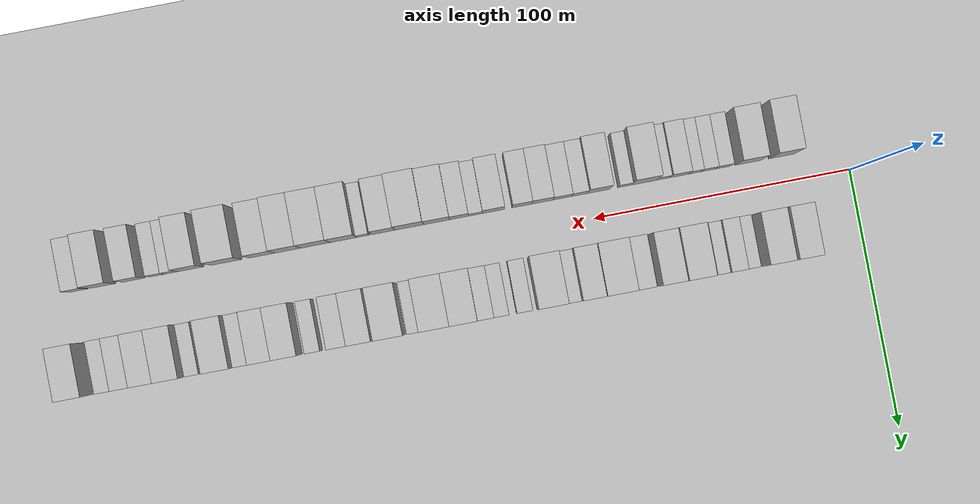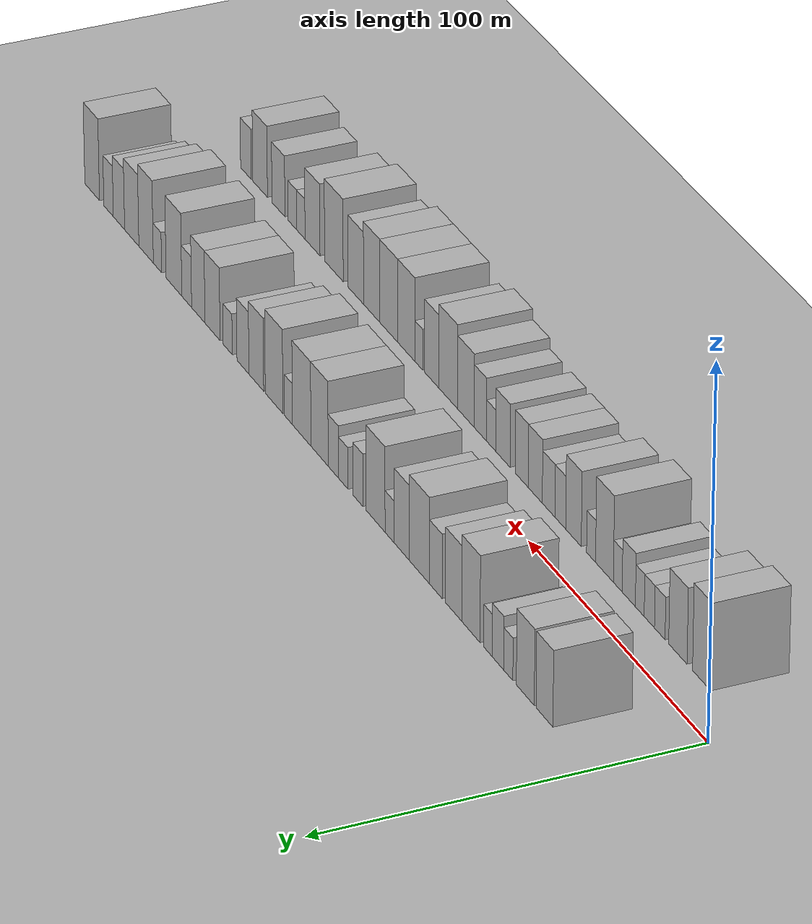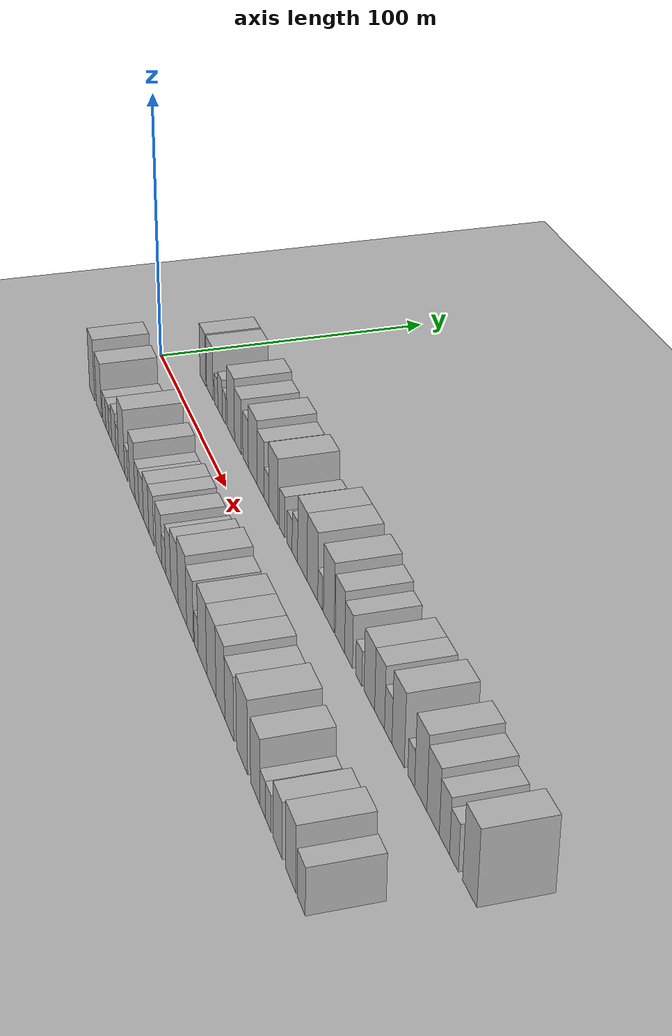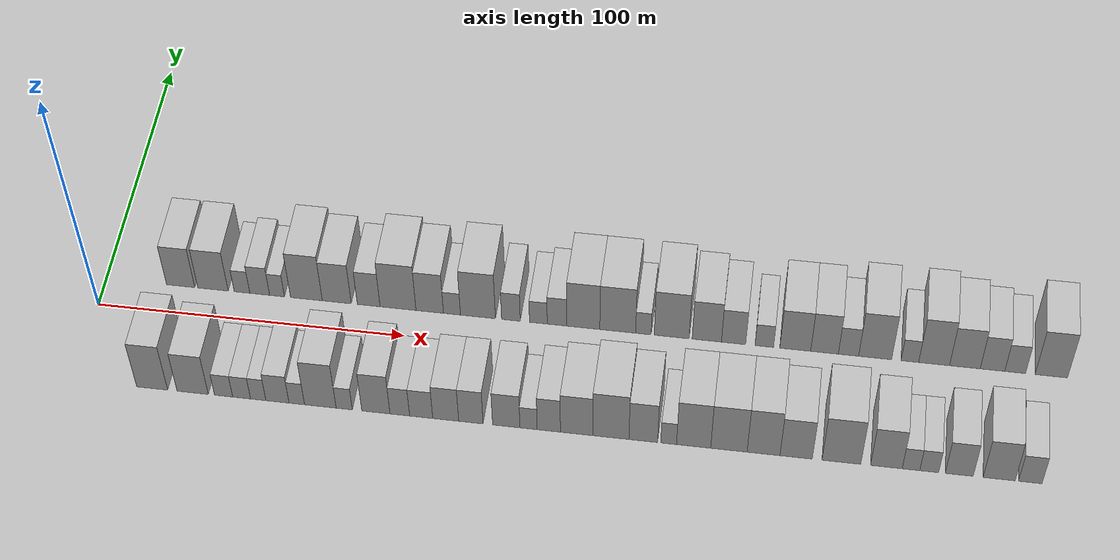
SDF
<?xml version="1.0" encoding="utf-8"?>

<sdf version="1.6">

   <world name="default">

      <gui fullscreen="0">

         <camera name="user_camera">

            <pose>-15 0 4.57585 0 0 0</pose>

            <view_controller>orbit</view_controller>

         </camera>

      </gui>

      <scene>

         <sky>

           <clouds>

             <speed>12</speed>

           </clouds>

         </sky>

         <ambient>0.4 0.4 0.4 1</ambient>

         <background>0.7 0.7 0.7 1</background>

         <shadows>1</shadows>

      </scene>

      <gravity>0 0 -9.8066</gravity>

      <magnetic_field>6e-06 2.3e-05 -4.2e-05</magnetic_field>

      <physics default="0" name="default_physics" type="ode">

         <ode>

            <solver>

               <type>quick</type>

               <iters>10</iters>

               <sor>1.0</sor>

               <use_dynamic_moi_rescaling>0</use_dynamic_moi_rescaling>

            </solver>

            <constraints>

               <cfm>0</cfm>

               <erp>0.2</erp>

               <contact_max_correcting_vel>100</contact_max_correcting_vel>

               <contact_surface_layer>0.001</contact_surface_layer>

            </constraints>

         </ode>

         <max_step_size>0.004</max_step_size>

         <real_time_factor>1</real_time_factor>

         <real_time_update_rate>250</real_time_update_rate>

      </physics>

      <light name="sun" type="directional">

         <cast_shadows>1</cast_shadows>

         <pose>0 0 10 0 0 0</pose>

         <diffuse>0.8 0.8 0.8 1</diffuse>

         <specular>0.2 0.2 0.2 1</specular>

         <attenuation>

            <range>1000</range>

            <constant>0.9</constant>

            <linear>0.01</linear>

            <quadratic>0.001</quadratic>

         </attenuation>

         <direction>-0.5 0.1 -0.9</direction>

      </light>

      <include>

         <name>ground_plane_1</name>

         <uri>model://HANNAS_ground_plane</uri>

         <pose>0 0 0  0 0 0</pose>

      </include>

      <include>

         <name>ground_plane_2</name>

         <uri>model://HANNAS_ground_plane</uri>

         <pose>100 0 0  0 0 0</pose>

      </include>

      <model name="building_1">

         <static>1</static>

         <pose frame="">24.6834 20.0000 0 0.000000 0.000000 1.570796</pose>

         <link name="link">

            <pose frame="">0 0 10.50 0 0 0</pose>

            <collision name="collision">

               <geometry>

                  <box>

                     <size>20.0000 9.3668 21.0000</size>

                  </box>

               </geometry>

               <max_contacts>10</max_contacts>

               <surface>

                  <contact>

                     <ode/>

                  </contact>

                  <bounce/>

                  <friction>

                     <torsional>

                        <ode/>

                     </torsional>

                     <ode/>

                  </friction>

               </surface>

            </collision>

            <visual name="visual">

               <cast_shadows>0</cast_shadows>

               <geometry>

                  <box>

                     <size>20.0000 9.3668 21.0000</size>

                  </box>

               </geometry>

               <material>

                  <script>

                     <uri>model://HANNAS_wall/materials/scripts</uri>

                     <uri>model://HANNAS_wall/materials/textures</uri>

                     <name>vrc/HANNAS_wall</name>

                  </script>

               </material>

            </visual>

            <self_collide>0</self_collide>

            <enable_wind>0</enable_wind>

            <kinematic>0</kinematic>

         </link>

      </model>

      <model name="building_2">

         <static>1</static>

         <pose frame="">35.3966 20.0000 0 0.000000 0.000000 1.570796</pose>

         <link name="link">

            <pose frame="">0 0 10.50 0 0 0</pose>

            <collision name="collision">

               <geometry>

                  <box>

                     <size>20.0000 10.0596 21.0000</size>

                  </box>

               </geometry>

               <max_contacts>10</max_contacts>

               <surface>

                  <contact>

                     <ode/>

                  </contact>

                  <bounce/>

                  <friction>

                     <torsional>

                        <ode/>

                     </torsional>

                     <ode/>

                  </friction>

               </surface>

            </collision>

            <visual name="visual">

               <cast_shadows>0</cast_shadows>

               <geometry>

                  <box>

                     <size>20.0000 10.0596 21.0000</size>

                  </box>

               </geometry>

               <material>

                  <script>

                     <uri>model://HANNAS_wall/materials/scripts</uri>

                     <uri>model://HANNAS_wall/materials/textures</uri>

                     <name>vrc/HANNAS_wall</name>

                  </script>

               </material>

            </visual>

            <self_collide>0</self_collide>

            <enable_wind>0</enable_wind>

            <kinematic>0</kinematic>

         </link>

      </model>

      <model name="building_3">

         <static>1</static>

         <pose frame="">45.0067 20.0000 0 0.000000 0.000000 1.570796</pose>

         <link name="link">

            <pose frame="">0 0 6.00 0 0 0</pose>

            <collision name="collision">

               <geometry>

                  <box>

                     <size>20.0000 5.1606 12.0000</size>

                  </box>

               </geometry>

               <max_contacts>10</max_contacts>

               <surface>

                  <contact>

                     <ode/>

                  </contact>

                  <bounce/>

                  <friction>

                     <torsional>

                        <ode/>

                     </torsional>

                     <ode/>

                  </friction>

               </surface>

            </collision>

            <visual name="visual">

               <cast_shadows>0</cast_shadows>

               <geometry>

                  <box>

                     <size>20.0000 5.1606 12.0000</size>

                  </box>

               </geometry>

               <material>

                  <script>

                     <uri>model://HANNAS_wall/materials/scripts</uri>

                     <uri>model://HANNAS_wall/materials/textures</uri>

                     <name>vrc/HANNAS_wall</name>

                  </script>

               </material>

            </visual>

            <self_collide>0</self_collide>

            <enable_wind>0</enable_wind>

            <kinematic>0</kinematic>

         </link>

      </model>

      <model name="building_4">

         <static>1</static>

         <pose frame="">50.8399 20.0000 0 0.000000 0.000000 1.570796</pose>

         <link name="link">

            <pose frame="">0 0 7.50 0 0 0</pose>

            <collision name="collision">

               <geometry>

                  <box>

                     <size>20.0000 6.5058 15.0000</size>

                  </box>

               </geometry>

               <max_contacts>10</max_contacts>

               <surface>

                  <contact>

                     <ode/>

                  </contact>

                  <bounce/>

                  <friction>

                     <torsional>

                        <ode/>

                     </torsional>

                     <ode/>

                  </friction>

               </surface>

            </collision>

            <visual name="visual">

               <cast_shadows>0</cast_shadows>

               <geometry>

                  <box>

                     <size>20.0000 6.5058 15.0000</size>

                  </box>

               </geometry>

               <material>

                  <script>

                     <uri>model://HANNAS_wall/materials/scripts</uri>

                     <uri>model://HANNAS_wall/materials/textures</uri>

                     <name>vrc/HANNAS_wall</name>

                  </script>

               </material>

            </visual>

            <self_collide>0</self_collide>

            <enable_wind>0</enable_wind>

            <kinematic>0</kinematic>

         </link>

      </model>

      <model name="building_5">

         <static>1</static>

         <pose frame="">56.5480 20.0000 0 0.000000 0.000000 1.570796</pose>

         <link name="link">

            <pose frame="">0 0 6.00 0 0 0</pose>

            <collision name="collision">

               <geometry>

                  <box>

                     <size>20.0000 4.9104 12.0000</size>

                  </box>

               </geometry>

               <max_contacts>10</max_contacts>

               <surface>

                  <contact>

                     <ode/>

                  </contact>

                  <bounce/>

                  <friction>

                     <torsional>

                        <ode/>

                     </torsional>

                     <ode/>

                  </friction>

               </surface>

            </collision>

            <visual name="visual">

               <cast_shadows>0</cast_shadows>

               <geometry>

                  <box>

                     <size>20.0000 4.9104 12.0000</size>

                  </box>

               </geometry>

               <material>

                  <script>

                     <uri>model://HANNAS_wall/materials/scripts</uri>

                     <uri>model://HANNAS_wall/materials/textures</uri>

                     <name>vrc/HANNAS_wall</name>

                  </script>

               </material>

            </visual>

            <self_collide>0</self_collide>

            <enable_wind>0</enable_wind>

            <kinematic>0</kinematic>

         </link>

      </model>

      <model name="building_6">

         <static>1</static>

         <pose frame="">66.2332 20.0000 0 0.000000 0.000000 1.570796</pose>

         <link name="link">

            <pose frame="">0 0 12.00 0 0 0</pose>

            <collision name="collision">

               <geometry>

                  <box>

                     <size>20.0000 10.4600 24.0000</size>

                  </box>

               </geometry>

               <max_contacts>10</max_contacts>

               <surface>

                  <contact>

                     <ode/>

                  </contact>

                  <bounce/>

                  <friction>

                     <torsional>

                        <ode/>

                     </torsional>

                     <ode/>

                  </friction>

               </surface>

            </collision>

            <visual name="visual">

               <cast_shadows>0</cast_shadows>

               <geometry>

                  <box>

                     <size>20.0000 10.4600 24.0000</size>

                  </box>

               </geometry>

               <material>

                  <script>

                     <uri>model://HANNAS_wall/materials/scripts</uri>

                     <uri>model://HANNAS_wall/materials/textures</uri>

                     <name>vrc/HANNAS_wall</name>

                  </script>

               </material>

            </visual>

            <self_collide>0</self_collide>

            <enable_wind>0</enable_wind>

            <kinematic>0</kinematic>

         </link>

      </model>

      <model name="building_7">

         <static>1</static>

         <pose frame="">76.2129 20.0000 0 0.000000 0.000000 1.570796</pose>

         <link name="link">

            <pose frame="">0 0 10.50 0 0 0</pose>

            <collision name="collision">

               <geometry>

                  <box>

                     <size>20.0000 9.4994 21.0000</size>

                  </box>

               </geometry>

               <max_contacts>10</max_contacts>

               <surface>

                  <contact>

                     <ode/>

                  </contact>

                  <bounce/>

                  <friction>

                     <torsional>

                        <ode/>

                     </torsional>

                     <ode/>

                  </friction>

               </surface>

            </collision>

            <visual name="visual">

               <cast_shadows>0</cast_shadows>

               <geometry>

                  <box>

                     <size>20.0000 9.4994 21.0000</size>

                  </box>

               </geometry>

               <material>

                  <script>

                     <uri>model://HANNAS_wall/materials/scripts</uri>

                     <uri>model://HANNAS_wall/materials/textures</uri>

                     <name>vrc/HANNAS_wall</name>

                  </script>

               </material>

            </visual>

            <self_collide>0</self_collide>

            <enable_wind>0</enable_wind>

            <kinematic>0</kinematic>

         </link>

      </model>

      <model name="building_8">

         <static>1</static>

         <pose frame="">86.6839 20.0000 0 0.000000 0.000000 1.570796</pose>

         <link name="link">

            <pose frame="">0 0 9.00 0 0 0</pose>

            <collision name="collision">

               <geometry>

                  <box>

                     <size>20.0000 7.4425 18.0000</size>

                  </box>

               </geometry>

               <max_contacts>10</max_contacts>

               <surface>

                  <contact>

                     <ode/>

                  </contact>

                  <bounce/>

                  <friction>

                     <torsional>

                        <ode/>

                     </torsional>

                     <ode/>

                  </friction>

               </surface>

            </collision>

            <visual name="visual">

               <cast_shadows>0</cast_shadows>

               <geometry>

                  <box>

                     <size>20.0000 7.4425 18.0000</size>

                  </box>

               </geometry>

               <material>

                  <script>

                     <uri>model://HANNAS_wall/materials/scripts</uri>

                     <uri>model://HANNAS_wall/materials/textures</uri>

                     <name>vrc/HANNAS_wall</name>

                  </script>

               </material>

            </visual>

            <self_collide>0</self_collide>

            <enable_wind>0</enable_wind>

            <kinematic>0</kinematic>

         </link>

      </model>

      <model name="building_9">

         <static>1</static>

         <pose frame="">96.2823 20.0000 0 0.000000 0.000000 1.570796</pose>

         <link name="link">

            <pose frame="">0 0 12.00 0 0 0</pose>

            <collision name="collision">

               <geometry>

                  <box>

                     <size>20.0000 11.7544 24.0000</size>

                  </box>

               </geometry>

               <max_contacts>10</max_contacts>

               <surface>

                  <contact>

                     <ode/>

                  </contact>

                  <bounce/>

                  <friction>

                     <torsional>

                        <ode/>

                     </torsional>

                     <ode/>

                  </friction>

               </surface>

            </collision>

            <visual name="visual">

               <cast_shadows>0</cast_shadows>

               <geometry>

                  <box>

                     <size>20.0000 11.7544 24.0000</size>

                  </box>

               </geometry>

               <material>

                  <script>

                     <uri>model://HANNAS_wall/materials/scripts</uri>

                     <uri>model://HANNAS_wall/materials/textures</uri>

                     <name>vrc/HANNAS_wall</name>

                  </script>

               </material>

            </visual>

            <self_collide>0</self_collide>

            <enable_wind>0</enable_wind>

            <kinematic>0</kinematic>

         </link>

      </model>

      <model name="building_10">

         <static>1</static>

         <pose frame="">106.6417 20.0000 0 0.000000 0.000000 1.570796</pose>

         <link name="link">

            <pose frame="">0 0 10.50 0 0 0</pose>

            <collision name="collision">

               <geometry>

                  <box>

                     <size>20.0000 8.9642 21.0000</size>

                  </box>

               </geometry>

               <max_contacts>10</max_contacts>

               <surface>

                  <contact>

                     <ode/>

                  </contact>

                  <bounce/>

                  <friction>

                     <torsional>

                        <ode/>

                     </torsional>

                     <ode/>

                  </friction>

               </surface>

            </collision>

            <visual name="visual">

               <cast_shadows>0</cast_shadows>

               <geometry>

                  <box>

                     <size>20.0000 8.9642 21.0000</size>

                  </box>

               </geometry>

               <material>

                  <script>

                     <uri>model://HANNAS_wall/materials/scripts</uri>

                     <uri>model://HANNAS_wall/materials/textures</uri>

                     <name>vrc/HANNAS_wall</name>

                  </script>

               </material>

            </visual>

            <self_collide>0</self_collide>

            <enable_wind>0</enable_wind>

            <kinematic>0</kinematic>

         </link>

      </model>

      <model name="building_11">

         <static>1</static>

         <pose frame="">113.8930 20.0000 0 0.000000 0.000000 1.570796</pose>

         <link name="link">

            <pose frame="">0 0 6.00 0 0 0</pose>

            <collision name="collision">

               <geometry>

                  <box>

                     <size>20.0000 5.5385 12.0000</size>

                  </box>

               </geometry>

               <max_contacts>10</max_contacts>

               <surface>

                  <contact>

                     <ode/>

                  </contact>

                  <bounce/>

                  <friction>

                     <torsional>

                        <ode/>

                     </torsional>

                     <ode/>

                  </friction>

               </surface>

            </collision>

            <visual name="visual">

               <cast_shadows>0</cast_shadows>

               <geometry>

                  <box>

                     <size>20.0000 5.5385 12.0000</size>

                  </box>

               </geometry>

               <material>

                  <script>

                     <uri>model://HANNAS_wall/materials/scripts</uri>

                     <uri>model://HANNAS_wall/materials/textures</uri>

                     <name>vrc/HANNAS_wall</name>

                  </script>

               </material>

            </visual>

            <self_collide>0</self_collide>

            <enable_wind>0</enable_wind>

            <kinematic>0</kinematic>

         </link>

      </model>

      <model name="building_12">

         <static>1</static>

         <pose frame="">122.3514 20.0000 0 0.000000 0.000000 1.570796</pose>

         <link name="link">

            <pose frame="">0 0 12.00 0 0 0</pose>

            <collision name="collision">

               <geometry>

                  <box>

                     <size>20.0000 11.3783 24.0000</size>

                  </box>

               </geometry>

               <max_contacts>10</max_contacts>

               <surface>

                  <contact>

                     <ode/>

                  </contact>

                  <bounce/>

                  <friction>

                     <torsional>

                        <ode/>

                     </torsional>

                     <ode/>

                  </friction>

               </surface>

            </collision>

            <visual name="visual">

               <cast_shadows>0</cast_shadows>

               <geometry>

                  <box>

                     <size>20.0000 11.3783 24.0000</size>

                  </box>

               </geometry>

               <material>

                  <script>

                     <uri>model://HANNAS_wall/materials/scripts</uri>

                     <uri>model://HANNAS_wall/materials/textures</uri>

                     <name>vrc/HANNAS_wall</name>

                  </script>

               </material>

            </visual>

            <self_collide>0</self_collide>

            <enable_wind>0</enable_wind>

            <kinematic>0</kinematic>

         </link>

      </model>

      <model name="building_13">

         <static>1</static>

         <pose frame="">133.0637 20.0000 0 0.000000 0.000000 1.570796</pose>

         <link name="link">

            <pose frame="">0 0 7.50 0 0 0</pose>

            <collision name="collision">

               <geometry>

                  <box>

                     <size>20.0000 6.0463 15.0000</size>

                  </box>

               </geometry>

               <max_contacts>10</max_contacts>

               <surface>

                  <contact>

                     <ode/>

                  </contact>

                  <bounce/>

                  <friction>

                     <torsional>

                        <ode/>

                     </torsional>

                     <ode/>

                  </friction>

               </surface>

            </collision>

            <visual name="visual">

               <cast_shadows>0</cast_shadows>

               <geometry>

                  <box>

                     <size>20.0000 6.0463 15.0000</size>

                  </box>

               </geometry>

               <material>

                  <script>

                     <uri>model://HANNAS_wall/materials/scripts</uri>

                     <uri>model://HANNAS_wall/materials/textures</uri>

                     <name>vrc/HANNAS_wall</name>

                  </script>

               </material>

            </visual>

            <self_collide>0</self_collide>

            <enable_wind>0</enable_wind>

            <kinematic>0</kinematic>

         </link>

      </model>

      <model name="building_14">

         <static>1</static>

         <pose frame="">141.9620 20.0000 0 0.000000 0.000000 1.570796</pose>

         <link name="link">

            <pose frame="">0 0 6.00 0 0 0</pose>

            <collision name="collision">

               <geometry>

                  <box>

                     <size>20.0000 5.7503 12.0000</size>

                  </box>

               </geometry>

               <max_contacts>10</max_contacts>

               <surface>

                  <contact>

                     <ode/>

                  </contact>

                  <bounce/>

                  <friction>

                     <torsional>

                        <ode/>

                     </torsional>

                     <ode/>

                  </friction>

               </surface>

            </collision>

            <visual name="visual">

               <cast_shadows>0</cast_shadows>

               <geometry>

                  <box>

                     <size>20.0000 5.7503 12.0000</size>

                  </box>

               </geometry>

               <material>

                  <script>

                     <uri>model://HANNAS_wall/materials/scripts</uri>

                     <uri>model://HANNAS_wall/materials/textures</uri>

                     <name>vrc/HANNAS_wall</name>

                  </script>

               </material>

            </visual>

            <self_collide>0</self_collide>

            <enable_wind>0</enable_wind>

            <kinematic>0</kinematic>

         </link>

      </model>

      <model name="building_15">

         <static>1</static>

         <pose frame="">148.0059 20.0000 0 0.000000 0.000000 1.570796</pose>

         <link name="link">

            <pose frame="">0 0 7.50 0 0 0</pose>

            <collision name="collision">

               <geometry>

                  <box>

                     <size>20.0000 6.3373 15.0000</size>

                  </box>

               </geometry>

               <max_contacts>10</max_contacts>

               <surface>

                  <contact>

                     <ode/>

                  </contact>

                  <bounce/>

                  <friction>

                     <torsional>

                        <ode/>

                     </torsional>

                     <ode/>

                  </friction>

               </surface>

            </collision>

            <visual name="visual">

               <cast_shadows>0</cast_shadows>

               <geometry>

                  <box>

                     <size>20.0000 6.3373 15.0000</size>

                  </box>

               </geometry>

               <material>

                  <script>

                     <uri>model://HANNAS_wall/materials/scripts</uri>

                     <uri>model://HANNAS_wall/materials/textures</uri>

                     <name>vrc/HANNAS_wall</name>

                  </script>

               </material>

            </visual>

            <self_collide>0</self_collide>

            <enable_wind>0</enable_wind>

            <kinematic>0</kinematic>

         </link>

      </model>

      <model name="building_16">

         <static>1</static>

         <pose frame="">156.4968 20.0000 0 0.000000 0.000000 1.570796</pose>

         <link name="link">

            <pose frame="">0 0 12.00 0 0 0</pose>

            <collision name="collision">

               <geometry>

                  <box>

                     <size>20.0000 10.6446 24.0000</size>

                  </box>

               </geometry>

               <max_contacts>10</max_contacts>

               <surface>

                  <contact>

                     <ode/>

                  </contact>

                  <bounce/>

                  <friction>

                     <torsional>

                        <ode/>

                     </torsional>

                     <ode/>

                  </friction>

               </surface>

            </collision>

            <visual name="visual">

               <cast_shadows>0</cast_shadows>

               <geometry>

                  <box>

                     <size>20.0000 10.6446 24.0000</size>

                  </box>

               </geometry>

               <material>

                  <script>

                     <uri>model://HANNAS_wall/materials/scripts</uri>

                     <uri>model://HANNAS_wall/materials/textures</uri>

                     <name>vrc/HANNAS_wall</name>

                  </script>

               </material>

            </visual>

            <self_collide>0</self_collide>

            <enable_wind>0</enable_wind>

            <kinematic>0</kinematic>

         </link>

      </model>

      <model name="building_17">

         <static>1</static>

         <pose frame="">167.5923 20.0000 0 0.000000 0.000000 1.570796</pose>

         <link name="link">

            <pose frame="">0 0 12.00 0 0 0</pose>

            <collision name="collision">

               <geometry>

                  <box>

                     <size>20.0000 11.5463 24.0000</size>

                  </box>

               </geometry>

               <max_contacts>10</max_contacts>

               <surface>

                  <contact>

                     <ode/>

                  </contact>

                  <bounce/>

                  <friction>

                     <torsional>

                        <ode/>

                     </torsional>

                     <ode/>

                  </friction>

               </surface>

            </collision>

            <visual name="visual">

               <cast_shadows>0</cast_shadows>

               <geometry>

                  <box>

                     <size>20.0000 11.5463 24.0000</size>

                  </box>

               </geometry>

               <material>

                  <script>

                     <uri>model://HANNAS_wall/materials/scripts</uri>

                     <uri>model://HANNAS_wall/materials/textures</uri>

                     <name>vrc/HANNAS_wall</name>

                  </script>

               </material>

            </visual>

            <self_collide>0</self_collide>

            <enable_wind>0</enable_wind>

            <kinematic>0</kinematic>

         </link>

      </model>

      <model name="building_18">

         <static>1</static>

         <pose frame="">175.8534 20.0000 0 0.000000 0.000000 1.570796</pose>

         <link name="link">

            <pose frame="">0 0 6.00 0 0 0</pose>

            <collision name="collision">

               <geometry>

                  <box>

                     <size>20.0000 4.9759 12.0000</size>

                  </box>

               </geometry>

               <max_contacts>10</max_contacts>

               <surface>

                  <contact>

                     <ode/>

                  </contact>

                  <bounce/>

                  <friction>

                     <torsional>

                        <ode/>

                     </torsional>

                     <ode/>

                  </friction>

               </surface>

            </collision>

            <visual name="visual">

               <cast_shadows>0</cast_shadows>

               <geometry>

                  <box>

                     <size>20.0000 4.9759 12.0000</size>

                  </box>

               </geometry>

               <material>

                  <script>

                     <uri>model://HANNAS_wall/materials/scripts</uri>

                     <uri>model://HANNAS_wall/materials/textures</uri>

                     <name>vrc/HANNAS_wall</name>

                  </script>

               </material>

            </visual>

            <self_collide>0</self_collide>

            <enable_wind>0</enable_wind>

            <kinematic>0</kinematic>

         </link>

      </model>

      <model name="building_19">

         <static>1</static>

         <pose frame="">184.9343 20.0000 0 0.000000 0.000000 1.570796</pose>

         <link name="link">

            <pose frame="">0 0 12.00 0 0 0</pose>

            <collision name="collision">

               <geometry>

                  <box>

                     <size>20.0000 11.1859 24.0000</size>

                  </box>

               </geometry>

               <max_contacts>10</max_contacts>

               <surface>

                  <contact>

                     <ode/>

                  </contact>

                  <bounce/>

                  <friction>

                     <torsional>

                        <ode/>

                     </torsional>

                     <ode/>

                  </friction>

               </surface>

            </collision>

            <visual name="visual">

               <cast_shadows>0</cast_shadows>

               <geometry>

                  <box>

                     <size>20.0000 11.1859 24.0000</size>

                  </box>

               </geometry>

               <material>

                  <script>

                     <uri>model://HANNAS_wall/materials/scripts</uri>

                     <uri>model://HANNAS_wall/materials/textures</uri>

                     <name>vrc/HANNAS_wall</name>

                  </script>

               </material>

            </visual>

            <self_collide>0</self_collide>

            <enable_wind>0</enable_wind>

            <kinematic>0</kinematic>

         </link>

      </model>

      <model name="building_20">

         <static>1</static>

         <pose frame="">196.2174 20.0000 0 0.000000 0.000000 1.570796</pose>

         <link name="link">

            <pose frame="">0 0 10.50 0 0 0</pose>

            <collision name="collision">

               <geometry>

                  <box>

                     <size>20.0000 9.3804 21.0000</size>

                  </box>

               </geometry>

               <max_contacts>10</max_contacts>

               <surface>

                  <contact>

                     <ode/>

                  </contact>

                  <bounce/>

                  <friction>

                     <torsional>

                        <ode/>

                     </torsional>

                     <ode/>

                  </friction>

               </surface>

            </collision>

            <visual name="visual">

               <cast_shadows>0</cast_shadows>

               <geometry>

                  <box>

                     <size>20.0000 9.3804 21.0000</size>

                  </box>

               </geometry>

               <material>

                  <script>

                     <uri>model://HANNAS_wall/materials/scripts</uri>

                     <uri>model://HANNAS_wall/materials/textures</uri>

                     <name>vrc/HANNAS_wall</name>

                  </script>

               </material>

            </visual>

            <self_collide>0</self_collide>

            <enable_wind>0</enable_wind>

            <kinematic>0</kinematic>

         </link>

      </model>

      <model name="building_21">

         <static>1</static>

         <pose frame="">204.7751 20.0000 0 0.000000 0.000000 1.570796</pose>

         <link name="link">

            <pose frame="">0 0 9.00 0 0 0</pose>

            <collision name="collision">

               <geometry>

                  <box>

                     <size>20.0000 7.7349 18.0000</size>

                  </box>

               </geometry>

               <max_contacts>10</max_contacts>

               <surface>

                  <contact>

                     <ode/>

                  </contact>

                  <bounce/>

                  <friction>

                     <torsional>

                        <ode/>

                     </torsional>

                     <ode/>

                  </friction>

               </surface>

            </collision>

            <visual name="visual">

               <cast_shadows>0</cast_shadows>

               <geometry>

                  <box>

                     <size>20.0000 7.7349 18.0000</size>

                  </box>

               </geometry>

               <material>

                  <script>

                     <uri>model://HANNAS_wall/materials/scripts</uri>

                     <uri>model://HANNAS_wall/materials/textures</uri>

                     <name>vrc/HANNAS_wall</name>

                  </script>

               </material>

            </visual>

            <self_collide>0</self_collide>

            <enable_wind>0</enable_wind>

            <kinematic>0</kinematic>

         </link>

      </model>

      <model name="building_22">

         <static>1</static>

         <pose frame="">214.5912 20.0000 0 0.000000 0.000000 1.570796</pose>

         <link name="link">

            <pose frame="">0 0 6.00 0 0 0</pose>

            <collision name="collision">

               <geometry>

                  <box>

                     <size>20.0000 5.8975 12.0000</size>

                  </box>

               </geometry>

               <max_contacts>10</max_contacts>

               <surface>

                  <contact>

                     <ode/>

                  </contact>

                  <bounce/>

                  <friction>

                     <torsional>

                        <ode/>

                     </torsional>

                     <ode/>

                  </friction>

               </surface>

            </collision>

            <visual name="visual">

               <cast_shadows>0</cast_shadows>

               <geometry>

                  <box>

                     <size>20.0000 5.8975 12.0000</size>

                  </box>

               </geometry>

               <material>

                  <script>

                     <uri>model://HANNAS_wall/materials/scripts</uri>

                     <uri>model://HANNAS_wall/materials/textures</uri>

                     <name>vrc/HANNAS_wall</name>

                  </script>

               </material>

            </visual>

            <self_collide>0</self_collide>

            <enable_wind>0</enable_wind>

            <kinematic>0</kinematic>

         </link>

      </model>

      <model name="building_23">

         <static>1</static>

         <pose frame="">224.4419 20.0000 0 0.000000 0.000000 1.570796</pose>

         <link name="link">

            <pose frame="">0 0 10.50 0 0 0</pose>

            <collision name="collision">

               <geometry>

                  <box>

                     <size>20.0000 9.8039 21.0000</size>

                  </box>

               </geometry>

               <max_contacts>10</max_contacts>

               <surface>

                  <contact>

                     <ode/>

                  </contact>

                  <bounce/>

                  <friction>

                     <torsional>

                        <ode/>

                     </torsional>

                     <ode/>

                  </friction>

               </surface>

            </collision>

            <visual name="visual">

               <cast_shadows>0</cast_shadows>

               <geometry>

                  <box>

                     <size>20.0000 9.8039 21.0000</size>

                  </box>

               </geometry>

               <material>

                  <script>

                     <uri>model://HANNAS_wall/materials/scripts</uri>

                     <uri>model://HANNAS_wall/materials/textures</uri>

                     <name>vrc/HANNAS_wall</name>

                  </script>

               </material>

            </visual>

            <self_collide>0</self_collide>

            <enable_wind>0</enable_wind>

            <kinematic>0</kinematic>

         </link>

      </model>

      <model name="building_24">

         <static>1</static>

         <pose frame="">233.7490 20.0000 0 0.000000 0.000000 1.570796</pose>

         <link name="link">

            <pose frame="">0 0 10.50 0 0 0</pose>

            <collision name="collision">

               <geometry>

                  <box>

                     <size>20.0000 8.8103 21.0000</size>

                  </box>

               </geometry>

               <max_contacts>10</max_contacts>

               <surface>

                  <contact>

                     <ode/>

                  </contact>

                  <bounce/>

                  <friction>

                     <torsional>

                        <ode/>

                     </torsional>

                     <ode/>

                  </friction>

               </surface>

            </collision>

            <visual name="visual">

               <cast_shadows>0</cast_shadows>

               <geometry>

                  <box>

                     <size>20.0000 8.8103 21.0000</size>

                  </box>

               </geometry>

               <material>

                  <script>

                     <uri>model://HANNAS_wall/materials/scripts</uri>

                     <uri>model://HANNAS_wall/materials/textures</uri>

                     <name>vrc/HANNAS_wall</name>

                  </script>

               </material>

            </visual>

            <self_collide>0</self_collide>

            <enable_wind>0</enable_wind>

            <kinematic>0</kinematic>

         </link>

      </model>

      <model name="building_25">

         <static>1</static>

         <pose frame="">241.3754 20.0000 0 0.000000 0.000000 1.570796</pose>

         <link name="link">

            <pose frame="">0 0 7.50 0 0 0</pose>

            <collision name="collision">

               <geometry>

                  <box>

                     <size>20.0000 6.4426 15.0000</size>

                  </box>

               </geometry>

               <max_contacts>10</max_contacts>

               <surface>

                  <contact>

                     <ode/>

                  </contact>

                  <bounce/>

                  <friction>

                     <torsional>

                        <ode/>

                     </torsional>

                     <ode/>

                  </friction>

               </surface>

            </collision>

            <visual name="visual">

               <cast_shadows>0</cast_shadows>

               <geometry>

                  <box>

                     <size>20.0000 6.4426 15.0000</size>

                  </box>

               </geometry>

               <material>

                  <script>

                     <uri>model://HANNAS_wall/materials/scripts</uri>

                     <uri>model://HANNAS_wall/materials/textures</uri>

                     <name>vrc/HANNAS_wall</name>

                  </script>

               </material>

            </visual>

            <self_collide>0</self_collide>

            <enable_wind>0</enable_wind>

            <kinematic>0</kinematic>

         </link>

      </model>

      <model name="building_26">

         <static>1</static>

         <pose frame="">249.8242 20.0000 0 0.000000 0.000000 1.570796</pose>

         <link name="link">

            <pose frame="">0 0 12.00 0 0 0</pose>

            <collision name="collision">

               <geometry>

                  <box>

                     <size>20.0000 10.4550 24.0000</size>

                  </box>

               </geometry>

               <max_contacts>10</max_contacts>

               <surface>

                  <contact>

                     <ode/>

                  </contact>

                  <bounce/>

                  <friction>

                     <torsional>

                        <ode/>

                     </torsional>

                     <ode/>

                  </friction>

               </surface>

            </collision>

            <visual name="visual">

               <cast_shadows>0</cast_shadows>

               <geometry>

                  <box>

                     <size>20.0000 10.4550 24.0000</size>

                  </box>

               </geometry>

               <material>

                  <script>

                     <uri>model://HANNAS_wall/materials/scripts</uri>

                     <uri>model://HANNAS_wall/materials/textures</uri>

                     <name>vrc/HANNAS_wall</name>

                  </script>

               </material>

            </visual>

            <self_collide>0</self_collide>

            <enable_wind>0</enable_wind>

            <kinematic>0</kinematic>

         </link>

      </model>

      <model name="building_27">

         <static>1</static>

         <pose frame="">260.8251 20.0000 0 0.000000 0.000000 1.570796</pose>

         <link name="link">

            <pose frame="">0 0 6.00 0 0 0</pose>

            <collision name="collision">

               <geometry>

                  <box>

                     <size>20.0000 5.5468 12.0000</size>

                  </box>

               </geometry>

               <max_contacts>10</max_contacts>

               <surface>

                  <contact>

                     <ode/>

                  </contact>

                  <bounce/>

                  <friction>

                     <torsional>

                        <ode/>

                     </torsional>

                     <ode/>

                  </friction>

               </surface>

            </collision>

            <visual name="visual">

               <cast_shadows>0</cast_shadows>

               <geometry>

                  <box>

                     <size>20.0000 5.5468 12.0000</size>

                  </box>

               </geometry>

               <material>

                  <script>

                     <uri>model://HANNAS_wall/materials/scripts</uri>

                     <uri>model://HANNAS_wall/materials/textures</uri>

                     <name>vrc/HANNAS_wall</name>

                  </script>

               </material>

            </visual>

            <self_collide>0</self_collide>

            <enable_wind>0</enable_wind>

            <kinematic>0</kinematic>

         </link>

      </model>

      <model name="building_28">

         <static>1</static>

         <pose frame="">268.4774 20.0000 0 0.000000 0.000000 1.570796</pose>

         <link name="link">

            <pose frame="">0 0 12.00 0 0 0</pose>

            <collision name="collision">

               <geometry>

                  <box>

                     <size>20.0000 9.7577 24.0000</size>

                  </box>

               </geometry>

               <max_contacts>10</max_contacts>

               <surface>

                  <contact>

                     <ode/>

                  </contact>

                  <bounce/>

                  <friction>

                     <torsional>

                        <ode/>

                     </torsional>

                     <ode/>

                  </friction>

               </surface>

            </collision>

            <visual name="visual">

               <cast_shadows>0</cast_shadows>

               <geometry>

                  <box>

                     <size>20.0000 9.7577 24.0000</size>

                  </box>

               </geometry>

               <material>

                  <script>

                     <uri>model://HANNAS_wall/materials/scripts</uri>

                     <uri>model://HANNAS_wall/materials/textures</uri>

                     <name>vrc/HANNAS_wall</name>

                  </script>

               </material>

            </visual>

            <self_collide>0</self_collide>

            <enable_wind>0</enable_wind>

            <kinematic>0</kinematic>

         </link>

      </model>

      <model name="building_29">

         <static>1</static>

         <pose frame="">278.1939 20.0000 0 0.000000 0.000000 1.570796</pose>

         <link name="link">

            <pose frame="">0 0 10.50 0 0 0</pose>

            <collision name="collision">

               <geometry>

                  <box>

                     <size>20.0000 9.6753 21.0000</size>

                  </box>

               </geometry>

               <max_contacts>10</max_contacts>

               <surface>

                  <contact>

                     <ode/>

                  </contact>

                  <bounce/>

                  <friction>

                     <torsional>

                        <ode/>

                     </torsional>

                     <ode/>

                  </friction>

               </surface>

            </collision>

            <visual name="visual">

               <cast_shadows>0</cast_shadows>

               <geometry>

                  <box>

                     <size>20.0000 9.6753 21.0000</size>

                  </box>

               </geometry>

               <material>

                  <script>

                     <uri>model://HANNAS_wall/materials/scripts</uri>

                     <uri>model://HANNAS_wall/materials/textures</uri>

                     <name>vrc/HANNAS_wall</name>

                  </script>

               </material>

            </visual>

            <self_collide>0</self_collide>

            <enable_wind>0</enable_wind>

            <kinematic>0</kinematic>

         </link>

      </model>

      <model name="building_30">

         <static>1</static>

         <pose frame="">286.8814 20.0000 0 0.000000 0.000000 1.570796</pose>

         <link name="link">

            <pose frame="">0 0 9.00 0 0 0</pose>

            <collision name="collision">

               <geometry>

                  <box>

                     <size>20.0000 7.6998 18.0000</size>

                  </box>

               </geometry>

               <max_contacts>10</max_contacts>

               <surface>

                  <contact>

                     <ode/>

                  </contact>

                  <bounce/>

                  <friction>

                     <torsional>

                        <ode/>

                     </torsional>

                     <ode/>

                  </friction>

               </surface>

            </collision>

            <visual name="visual">

               <cast_shadows>0</cast_shadows>

               <geometry>

                  <box>

                     <size>20.0000 7.6998 18.0000</size>

                  </box>

               </geometry>

               <material>

                  <script>

                     <uri>model://HANNAS_wall/materials/scripts</uri>

                     <uri>model://HANNAS_wall/materials/textures</uri>

                     <name>vrc/HANNAS_wall</name>

                  </script>

               </material>

            </visual>

            <self_collide>0</self_collide>

            <enable_wind>0</enable_wind>

            <kinematic>0</kinematic>

         </link>

      </model>

      <model name="building_31">

         <static>1</static>

         <pose frame="">293.9942 20.0000 0 0.000000 0.000000 1.570796</pose>

         <link name="link">

            <pose frame="">0 0 7.50 0 0 0</pose>

            <collision name="collision">

               <geometry>

                  <box>

                     <size>20.0000 6.5258 15.0000</size>

                  </box>

               </geometry>

               <max_contacts>10</max_contacts>

               <surface>

                  <contact>

                     <ode/>

                  </contact>

                  <bounce/>

                  <friction>

                     <torsional>

                        <ode/>

                     </torsional>

                     <ode/>

                  </friction>

               </surface>

            </collision>

            <visual name="visual">

               <cast_shadows>0</cast_shadows>

               <geometry>

                  <box>

                     <size>20.0000 6.5258 15.0000</size>

                  </box>

               </geometry>

               <material>

                  <script>

                     <uri>model://HANNAS_wall/materials/scripts</uri>

                     <uri>model://HANNAS_wall/materials/textures</uri>

                     <name>vrc/HANNAS_wall</name>

                  </script>

               </material>

            </visual>

            <self_collide>0</self_collide>

            <enable_wind>0</enable_wind>

            <kinematic>0</kinematic>

         </link>

      </model>

      <model name="building_32">

         <static>1</static>

         <pose frame="">305.3265 20.0000 0 0.000000 0.000000 1.570796</pose>

         <link name="link">

            <pose frame="">0 0 12.00 0 0 0</pose>

            <collision name="collision">

               <geometry>

                  <box>

                     <size>20.0000 10.1388 24.0000</size>

                  </box>

               </geometry>

               <max_contacts>10</max_contacts>

               <surface>

                  <contact>

                     <ode/>

                  </contact>

                  <bounce/>

                  <friction>

                     <torsional>

                        <ode/>

                     </torsional>

                     <ode/>

                  </friction>

               </surface>

            </collision>

            <visual name="visual">

               <cast_shadows>0</cast_shadows>

               <geometry>

                  <box>

                     <size>20.0000 10.1388 24.0000</size>

                  </box>

               </geometry>

               <material>

                  <script>

                     <uri>model://HANNAS_wall/materials/scripts</uri>

                     <uri>model://HANNAS_wall/materials/textures</uri>

                     <name>vrc/HANNAS_wall</name>

                  </script>

               </material>

            </visual>

            <self_collide>0</self_collide>

            <enable_wind>0</enable_wind>

            <kinematic>0</kinematic>

         </link>

      </model>

      <model name="building_33">

         <static>1</static>

         <pose frame="">24.9753 -20.0000 0 0.000000 0.000000 1.570796</pose>

         <link name="link">

            <pose frame="">0 0 12.00 0 0 0</pose>

            <collision name="collision">

               <geometry>

                  <box>

                     <size>20.0000 9.9506 24.0000</size>

                  </box>

               </geometry>

               <max_contacts>10</max_contacts>

               <surface>

                  <contact>

                     <ode/>

                  </contact>

                  <bounce/>

                  <friction>

                     <torsional>

                        <ode/>

                     </torsional>

                     <ode/>

                  </friction>

               </surface>

            </collision>

            <visual name="visual">

               <cast_shadows>0</cast_shadows>

               <geometry>

                  <box>

                     <size>20.0000 9.9506 24.0000</size>

                  </box>

               </geometry>

               <material>

                  <script>

                     <uri>model://HANNAS_wall/materials/scripts</uri>

                     <uri>model://HANNAS_wall/materials/textures</uri>

                     <name>vrc/HANNAS_wall</name>

                  </script>

               </material>

            </visual>

            <self_collide>0</self_collide>

            <enable_wind>0</enable_wind>

            <kinematic>0</kinematic>

         </link>

      </model>

      <model name="building_34">

         <static>1</static>

         <pose frame="">37.9530 -20.0000 0 0.000000 0.000000 1.570796</pose>

         <link name="link">

            <pose frame="">0 0 10.50 0 0 0</pose>

            <collision name="collision">

               <geometry>

                  <box>

                     <size>20.0000 10.0048 21.0000</size>

                  </box>

               </geometry>

               <max_contacts>10</max_contacts>

               <surface>

                  <contact>

                     <ode/>

                  </contact>

                  <bounce/>

                  <friction>

                     <torsional>

                        <ode/>

                     </torsional>

                     <ode/>

                  </friction>

               </surface>

            </collision>

            <visual name="visual">

               <cast_shadows>0</cast_shadows>

               <geometry>

                  <box>

                     <size>20.0000 10.0048 21.0000</size>

                  </box>

               </geometry>

               <material>

                  <script>

                     <uri>model://HANNAS_wall/materials/scripts</uri>

                     <uri>model://HANNAS_wall/materials/textures</uri>

                     <name>vrc/HANNAS_wall</name>

                  </script>

               </material>

            </visual>

            <self_collide>0</self_collide>

            <enable_wind>0</enable_wind>

            <kinematic>0</kinematic>

         </link>

      </model>

      <model name="building_35">

         <static>1</static>

         <pose frame="">47.8669 -20.0000 0 0.000000 0.000000 1.570796</pose>

         <link name="link">

            <pose frame="">0 0 6.00 0 0 0</pose>

            <collision name="collision">

               <geometry>

                  <box>

                     <size>20.0000 5.8230 12.0000</size>

                  </box>

               </geometry>

               <max_contacts>10</max_contacts>

               <surface>

                  <contact>

                     <ode/>

                  </contact>

                  <bounce/>

                  <friction>

                     <torsional>

                        <ode/>

                     </torsional>

                     <ode/>

                  </friction>

               </surface>

            </collision>

            <visual name="visual">

               <cast_shadows>0</cast_shadows>

               <geometry>

                  <box>

                     <size>20.0000 5.8230 12.0000</size>

                  </box>

               </geometry>

               <material>

                  <script>

                     <uri>model://HANNAS_wall/materials/scripts</uri>

                     <uri>model://HANNAS_wall/materials/textures</uri>

                     <name>vrc/HANNAS_wall</name>

                  </script>

               </material>

            </visual>

            <self_collide>0</self_collide>

            <enable_wind>0</enable_wind>

            <kinematic>0</kinematic>

         </link>

      </model>

      <model name="building_36">

         <static>1</static>

         <pose frame="">53.6267 -20.0000 0 0.000000 0.000000 1.570796</pose>

         <link name="link">

            <pose frame="">0 0 6.00 0 0 0</pose>

            <collision name="collision">

               <geometry>

                  <box>

                     <size>20.0000 5.6967 12.0000</size>

                  </box>

               </geometry>

               <max_contacts>10</max_contacts>

               <surface>

                  <contact>

                     <ode/>

                  </contact>

                  <bounce/>

                  <friction>

                     <torsional>

                        <ode/>

                     </torsional>

                     <ode/>

                  </friction>

               </surface>

            </collision>

            <visual name="visual">

               <cast_shadows>0</cast_shadows>

               <geometry>

                  <box>

                     <size>20.0000 5.6967 12.0000</size>

                  </box>

               </geometry>

               <material>

                  <script>

                     <uri>model://HANNAS_wall/materials/scripts</uri>

                     <uri>model://HANNAS_wall/materials/textures</uri>

                     <name>vrc/HANNAS_wall</name>

                  </script>

               </material>

            </visual>

            <self_collide>0</self_collide>

            <enable_wind>0</enable_wind>

            <kinematic>0</kinematic>

         </link>

      </model>

      <model name="building_37">

         <static>1</static>

         <pose frame="">58.9188 -20.0000 0 0.000000 0.000000 1.570796</pose>

         <link name="link">

            <pose frame="">0 0 6.00 0 0 0</pose>

            <collision name="collision">

               <geometry>

                  <box>

                     <size>20.0000 4.8874 12.0000</size>

                  </box>

               </geometry>

               <max_contacts>10</max_contacts>

               <surface>

                  <contact>

                     <ode/>

                  </contact>

                  <bounce/>

                  <friction>

                     <torsional>

                        <ode/>

                     </torsional>

                     <ode/>

                  </friction>

               </surface>

            </collision>

            <visual name="visual">

               <cast_shadows>0</cast_shadows>

               <geometry>

                  <box>

                     <size>20.0000 4.8874 12.0000</size>

                  </box>

               </geometry>

               <material>

                  <script>

                     <uri>model://HANNAS_wall/materials/scripts</uri>

                     <uri>model://HANNAS_wall/materials/textures</uri>

                     <name>vrc/HANNAS_wall</name>

                  </script>

               </material>

            </visual>

            <self_collide>0</self_collide>

            <enable_wind>0</enable_wind>

            <kinematic>0</kinematic>

         </link>

      </model>

      <model name="building_38">

         <static>1</static>

         <pose frame="">65.0419 -20.0000 0 0.000000 0.000000 1.570796</pose>

         <link name="link">

            <pose frame="">0 0 7.50 0 0 0</pose>

            <collision name="collision">

               <geometry>

                  <box>

                     <size>20.0000 7.3588 15.0000</size>

                  </box>

               </geometry>

               <max_contacts>10</max_contacts>

               <surface>

                  <contact>

                     <ode/>

                  </contact>

                  <bounce/>

                  <friction>

                     <torsional>

                        <ode/>

                     </torsional>

                     <ode/>

                  </friction>

               </surface>

            </collision>

            <visual name="visual">

               <cast_shadows>0</cast_shadows>

               <geometry>

                  <box>

                     <size>20.0000 7.3588 15.0000</size>

                  </box>

               </geometry>

               <material>

                  <script>

                     <uri>model://HANNAS_wall/materials/scripts</uri>

                     <uri>model://HANNAS_wall/materials/textures</uri>

                     <name>vrc/HANNAS_wall</name>

                  </script>

               </material>

            </visual>

            <self_collide>0</self_collide>

            <enable_wind>0</enable_wind>

            <kinematic>0</kinematic>

         </link>

      </model>

      <model name="building_39">

         <static>1</static>

         <pose frame="">71.2017 -20.0000 0 0.000000 0.000000 1.570796</pose>

         <link name="link">

            <pose frame="">0 0 6.00 0 0 0</pose>

            <collision name="collision">

               <geometry>

                  <box>

                     <size>20.0000 4.9608 12.0000</size>

                  </box>

               </geometry>

               <max_contacts>10</max_contacts>

               <surface>

                  <contact>

                     <ode/>

                  </contact>

                  <bounce/>

                  <friction>

                     <torsional>

                        <ode/>

                     </torsional>

                     <ode/>

                  </friction>

               </surface>

            </collision>

            <visual name="visual">

               <cast_shadows>0</cast_shadows>

               <geometry>

                  <box>

                     <size>20.0000 4.9608 12.0000</size>

                  </box>

               </geometry>

               <material>

                  <script>

                     <uri>model://HANNAS_wall/materials/scripts</uri>

                     <uri>model://HANNAS_wall/materials/textures</uri>

                     <name>vrc/HANNAS_wall</name>

                  </script>

               </material>

            </visual>

            <self_collide>0</self_collide>

            <enable_wind>0</enable_wind>

            <kinematic>0</kinematic>

         </link>

      </model>

      <model name="building_40">

         <static>1</static>

         <pose frame="">78.7000 -20.0000 0 0.000000 0.000000 1.570796</pose>

         <link name="link">

            <pose frame="">0 0 12.00 0 0 0</pose>

            <collision name="collision">

               <geometry>

                  <box>

                     <size>20.0000 10.0357 24.0000</size>

                  </box>

               </geometry>

               <max_contacts>10</max_contacts>

               <surface>

                  <contact>

                     <ode/>

                  </contact>

                  <bounce/>

                  <friction>

                     <torsional>

                        <ode/>

                     </torsional>

                     <ode/>

                  </friction>

               </surface>

            </collision>

            <visual name="visual">

               <cast_shadows>0</cast_shadows>

               <geometry>

                  <box>

                     <size>20.0000 10.0357 24.0000</size>

                  </box>

               </geometry>

               <material>

                  <script>

                     <uri>model://HANNAS_wall/materials/scripts</uri>

                     <uri>model://HANNAS_wall/materials/textures</uri>

                     <name>vrc/HANNAS_wall</name>

                  </script>

               </material>

            </visual>

            <self_collide>0</self_collide>

            <enable_wind>0</enable_wind>

            <kinematic>0</kinematic>

         </link>

      </model>

      <model name="building_41">

         <static>1</static>

         <pose frame="">86.2831 -20.0000 0 0.000000 0.000000 1.570796</pose>

         <link name="link">

            <pose frame="">0 0 6.00 0 0 0</pose>

            <collision name="collision">

               <geometry>

                  <box>

                     <size>20.0000 5.1305 12.0000</size>

                  </box>

               </geometry>

               <max_contacts>10</max_contacts>

               <surface>

                  <contact>

                     <ode/>

                  </contact>

                  <bounce/>

                  <friction>

                     <torsional>

                        <ode/>

                     </torsional>

                     <ode/>

                  </friction>

               </surface>

            </collision>

            <visual name="visual">

               <cast_shadows>0</cast_shadows>

               <geometry>

                  <box>

                     <size>20.0000 5.1305 12.0000</size>

                  </box>

               </geometry>

               <material>

                  <script>

                     <uri>model://HANNAS_wall/materials/scripts</uri>

                     <uri>model://HANNAS_wall/materials/textures</uri>

                     <name>vrc/HANNAS_wall</name>

                  </script>

               </material>

            </visual>

            <self_collide>0</self_collide>

            <enable_wind>0</enable_wind>

            <kinematic>0</kinematic>

         </link>

      </model>

      <model name="building_42">

         <static>1</static>

         <pose frame="">96.3100 -20.0000 0 0.000000 0.000000 1.570796</pose>

         <link name="link">

            <pose frame="">0 0 10.50 0 0 0</pose>

            <collision name="collision">

               <geometry>

                  <box>

                     <size>20.0000 8.9233 21.0000</size>

                  </box>

               </geometry>

               <max_contacts>10</max_contacts>

               <surface>

                  <contact>

                     <ode/>

                  </contact>

                  <bounce/>

                  <friction>

                     <torsional>

                        <ode/>

                     </torsional>

                     <ode/>

                  </friction>

               </surface>

            </collision>

            <visual name="visual">

               <cast_shadows>0</cast_shadows>

               <geometry>

                  <box>

                     <size>20.0000 8.9233 21.0000</size>

                  </box>

               </geometry>

               <material>

                  <script>

                     <uri>model://HANNAS_wall/materials/scripts</uri>

                     <uri>model://HANNAS_wall/materials/textures</uri>

                     <name>vrc/HANNAS_wall</name>

                  </script>

               </material>

            </visual>

            <self_collide>0</self_collide>

            <enable_wind>0</enable_wind>

            <kinematic>0</kinematic>

         </link>

      </model>

      <model name="building_43">

         <static>1</static>

         <pose frame="">103.8751 -20.0000 0 0.000000 0.000000 1.570796</pose>

         <link name="link">

            <pose frame="">0 0 7.50 0 0 0</pose>

            <collision name="collision">

               <geometry>

                  <box>

                     <size>20.0000 6.2070 15.0000</size>

                  </box>

               </geometry>

               <max_contacts>10</max_contacts>

               <surface>

                  <contact>

                     <ode/>

                  </contact>

                  <bounce/>

                  <friction>

                     <torsional>

                        <ode/>

                     </torsional>

                     <ode/>

                  </friction>

               </surface>

            </collision>

            <visual name="visual">

               <cast_shadows>0</cast_shadows>

               <geometry>

                  <box>

                     <size>20.0000 6.2070 15.0000</size>

                  </box>

               </geometry>

               <material>

                  <script>

                     <uri>model://HANNAS_wall/materials/scripts</uri>

                     <uri>model://HANNAS_wall/materials/textures</uri>

                     <name>vrc/HANNAS_wall</name>

                  </script>

               </material>

            </visual>

            <self_collide>0</self_collide>

            <enable_wind>0</enable_wind>

            <kinematic>0</kinematic>

         </link>

      </model>

      <model name="building_44">

         <static>1</static>

         <pose frame="">110.6280 -20.0000 0 0.000000 0.000000 1.570796</pose>

         <link name="link">

            <pose frame="">0 0 7.50 0 0 0</pose>

            <collision name="collision">

               <geometry>

                  <box>

                     <size>20.0000 7.2988 15.0000</size>

                  </box>

               </geometry>

               <max_contacts>10</max_contacts>

               <surface>

                  <contact>

                     <ode/>

                  </contact>

                  <bounce/>

                  <friction>

                     <torsional>

                        <ode/>

                     </torsional>

                     <ode/>

                  </friction>

               </surface>

            </collision>

            <visual name="visual">

               <cast_shadows>0</cast_shadows>

               <geometry>

                  <box>

                     <size>20.0000 7.2988 15.0000</size>

                  </box>

               </geometry>

               <material>

                  <script>

                     <uri>model://HANNAS_wall/materials/scripts</uri>

                     <uri>model://HANNAS_wall/materials/textures</uri>

                     <name>vrc/HANNAS_wall</name>

                  </script>

               </material>

            </visual>

            <self_collide>0</self_collide>

            <enable_wind>0</enable_wind>

            <kinematic>0</kinematic>

         </link>

      </model>

      <model name="building_45">

         <static>1</static>

         <pose frame="">118.3659 -20.0000 0 0.000000 0.000000 1.570796</pose>

         <link name="link">

            <pose frame="">0 0 9.00 0 0 0</pose>

            <collision name="collision">

               <geometry>

                  <box>

                     <size>20.0000 8.1769 18.0000</size>

                  </box>

               </geometry>

               <max_contacts>10</max_contacts>

               <surface>

                  <contact>

                     <ode/>

                  </contact>

                  <bounce/>

                  <friction>

                     <torsional>

                        <ode/>

                     </torsional>

                     <ode/>

                  </friction>

               </surface>

            </collision>

            <visual name="visual">

               <cast_shadows>0</cast_shadows>

               <geometry>

                  <box>

                     <size>20.0000 8.1769 18.0000</size>

                  </box>

               </geometry>

               <material>

                  <script>

                     <uri>model://HANNAS_wall/materials/scripts</uri>

                     <uri>model://HANNAS_wall/materials/textures</uri>

                     <name>vrc/HANNAS_wall</name>

                  </script>

               </material>

            </visual>

            <self_collide>0</self_collide>

            <enable_wind>0</enable_wind>

            <kinematic>0</kinematic>

         </link>

      </model>

      <model name="building_46">

         <static>1</static>

         <pose frame="">126.2881 -20.0000 0 0.000000 0.000000 1.570796</pose>

         <link name="link">

            <pose frame="">0 0 9.00 0 0 0</pose>

            <collision name="collision">

               <geometry>

                  <box>

                     <size>20.0000 7.6676 18.0000</size>

                  </box>

               </geometry>

               <max_contacts>10</max_contacts>

               <surface>

                  <contact>

                     <ode/>

                  </contact>

                  <bounce/>

                  <friction>

                     <torsional>

                        <ode/>

                     </torsional>

                     <ode/>

                  </friction>

               </surface>

            </collision>

            <visual name="visual">

               <cast_shadows>0</cast_shadows>

               <geometry>

                  <box>

                     <size>20.0000 7.6676 18.0000</size>

                  </box>

               </geometry>

               <material>

                  <script>

                     <uri>model://HANNAS_wall/materials/scripts</uri>

                     <uri>model://HANNAS_wall/materials/textures</uri>

                     <name>vrc/HANNAS_wall</name>

                  </script>

               </material>

            </visual>

            <self_collide>0</self_collide>

            <enable_wind>0</enable_wind>

            <kinematic>0</kinematic>

         </link>

      </model>

      <model name="building_47">

         <static>1</static>

         <pose frame="">137.4050 -20.0000 0 0.000000 0.000000 1.570796</pose>

         <link name="link">

            <pose frame="">0 0 9.00 0 0 0</pose>

            <collision name="collision">

               <geometry>

                  <box>

                     <size>20.0000 8.5662 18.0000</size>

                  </box>

               </geometry>

               <max_contacts>10</max_contacts>

               <surface>

                  <contact>

                     <ode/>

                  </contact>

                  <bounce/>

                  <friction>

                     <torsional>

                        <ode/>

                     </torsional>

                     <ode/>

                  </friction>

               </surface>

            </collision>

            <visual name="visual">

               <cast_shadows>0</cast_shadows>

               <geometry>

                  <box>

                     <size>20.0000 8.5662 18.0000</size>

                  </box>

               </geometry>

               <material>

                  <script>

                     <uri>model://HANNAS_wall/materials/scripts</uri>

                     <uri>model://HANNAS_wall/materials/textures</uri>

                     <name>vrc/HANNAS_wall</name>

                  </script>

               </material>

            </visual>

            <self_collide>0</self_collide>

            <enable_wind>0</enable_wind>

            <kinematic>0</kinematic>

         </link>

      </model>

      <model name="building_48">

         <static>1</static>

         <pose frame="">144.3906 -20.0000 0 0.000000 0.000000 1.570796</pose>

         <link name="link">

            <pose frame="">0 0 6.00 0 0 0</pose>

            <collision name="collision">

               <geometry>

                  <box>

                     <size>20.0000 5.4049 12.0000</size>

                  </box>

               </geometry>

               <max_contacts>10</max_contacts>

               <surface>

                  <contact>

                     <ode/>

                  </contact>

                  <bounce/>

                  <friction>

                     <torsional>

                        <ode/>

                     </torsional>

                     <ode/>

                  </friction>

               </surface>

            </collision>

            <visual name="visual">

               <cast_shadows>0</cast_shadows>

               <geometry>

                  <box>

                     <size>20.0000 5.4049 12.0000</size>

                  </box>

               </geometry>

               <material>

                  <script>

                     <uri>model://HANNAS_wall/materials/scripts</uri>

                     <uri>model://HANNAS_wall/materials/textures</uri>

                     <name>vrc/HANNAS_wall</name>

                  </script>

               </material>

            </visual>

            <self_collide>0</self_collide>

            <enable_wind>0</enable_wind>

            <kinematic>0</kinematic>

         </link>

      </model>

      <model name="building_49">

         <static>1</static>

         <pose frame="">150.7303 -20.0000 0 0.000000 0.000000 1.570796</pose>

         <link name="link">

            <pose frame="">0 0 9.00 0 0 0</pose>

            <collision name="collision">

               <geometry>

                  <box>

                     <size>20.0000 7.2745 18.0000</size>

                  </box>

               </geometry>

               <max_contacts>10</max_contacts>

               <surface>

                  <contact>

                     <ode/>

                  </contact>

                  <bounce/>

                  <friction>

                     <torsional>

                        <ode/>

                     </torsional>

                     <ode/>

                  </friction>

               </surface>

            </collision>

            <visual name="visual">

               <cast_shadows>0</cast_shadows>

               <geometry>

                  <box>

                     <size>20.0000 7.2745 18.0000</size>

                  </box>

               </geometry>

               <material>

                  <script>

                     <uri>model://HANNAS_wall/materials/scripts</uri>

                     <uri>model://HANNAS_wall/materials/textures</uri>

                     <name>vrc/HANNAS_wall</name>

                  </script>

               </material>

            </visual>

            <self_collide>0</self_collide>

            <enable_wind>0</enable_wind>

            <kinematic>0</kinematic>

         </link>

      </model>

      <model name="building_50">

         <static>1</static>

         <pose frame="">159.4050 -20.0000 0 0.000000 0.000000 1.570796</pose>

         <link name="link">

            <pose frame="">0 0 10.50 0 0 0</pose>

            <collision name="collision">

               <geometry>

                  <box>

                     <size>20.0000 10.0749 21.0000</size>

                  </box>

               </geometry>

               <max_contacts>10</max_contacts>

               <surface>

                  <contact>

                     <ode/>

                  </contact>

                  <bounce/>

                  <friction>

                     <torsional>

                        <ode/>

                     </torsional>

                     <ode/>

                  </friction>

               </surface>

            </collision>

            <visual name="visual">

               <cast_shadows>0</cast_shadows>

               <geometry>

                  <box>

                     <size>20.0000 10.0749 21.0000</size>

                  </box>

               </geometry>

               <material>

                  <script>

                     <uri>model://HANNAS_wall/materials/scripts</uri>

                     <uri>model://HANNAS_wall/materials/textures</uri>

                     <name>vrc/HANNAS_wall</name>

                  </script>

               </material>

            </visual>

            <self_collide>0</self_collide>

            <enable_wind>0</enable_wind>

            <kinematic>0</kinematic>

         </link>

      </model>

      <model name="building_51">

         <static>1</static>

         <pose frame="">170.0865 -20.0000 0 0.000000 0.000000 1.570796</pose>

         <link name="link">

            <pose frame="">0 0 12.00 0 0 0</pose>

            <collision name="collision">

               <geometry>

                  <box>

                     <size>20.0000 11.2882 24.0000</size>

                  </box>

               </geometry>

               <max_contacts>10</max_contacts>

               <surface>

                  <contact>

                     <ode/>

                  </contact>

                  <bounce/>

                  <friction>

                     <torsional>

                        <ode/>

                     </torsional>

                     <ode/>

                  </friction>

               </surface>

            </collision>

            <visual name="visual">

               <cast_shadows>0</cast_shadows>

               <geometry>

                  <box>

                     <size>20.0000 11.2882 24.0000</size>

                  </box>

               </geometry>

               <material>

                  <script>

                     <uri>model://HANNAS_wall/materials/scripts</uri>

                     <uri>model://HANNAS_wall/materials/textures</uri>

                     <name>vrc/HANNAS_wall</name>

                  </script>

               </material>

            </visual>

            <self_collide>0</self_collide>

            <enable_wind>0</enable_wind>

            <kinematic>0</kinematic>

         </link>

      </model>

      <model name="building_52">

         <static>1</static>

         <pose frame="">180.1830 -20.0000 0 0.000000 0.000000 1.570796</pose>

         <link name="link">

            <pose frame="">0 0 10.50 0 0 0</pose>

            <collision name="collision">

               <geometry>

                  <box>

                     <size>20.0000 8.9048 21.0000</size>

                  </box>

               </geometry>

               <max_contacts>10</max_contacts>

               <surface>

                  <contact>

                     <ode/>

                  </contact>

                  <bounce/>

                  <friction>

                     <torsional>

                        <ode/>

                     </torsional>

                     <ode/>

                  </friction>

               </surface>

            </collision>

            <visual name="visual">

               <cast_shadows>0</cast_shadows>

               <geometry>

                  <box>

                     <size>20.0000 8.9048 21.0000</size>

                  </box>

               </geometry>

               <material>

                  <script>

                     <uri>model://HANNAS_wall/materials/scripts</uri>

                     <uri>model://HANNAS_wall/materials/textures</uri>

                     <name>vrc/HANNAS_wall</name>

                  </script>

               </material>

            </visual>

            <self_collide>0</self_collide>

            <enable_wind>0</enable_wind>

            <kinematic>0</kinematic>

         </link>

      </model>

      <model name="building_53">

         <static>1</static>

         <pose frame="">188.0749 -20.0000 0 0.000000 0.000000 1.570796</pose>

         <link name="link">

            <pose frame="">0 0 6.00 0 0 0</pose>

            <collision name="collision">

               <geometry>

                  <box>

                     <size>20.0000 4.8788 12.0000</size>

                  </box>

               </geometry>

               <max_contacts>10</max_contacts>

               <surface>

                  <contact>

                     <ode/>

                  </contact>

                  <bounce/>

                  <friction>

                     <torsional>

                        <ode/>

                     </torsional>

                     <ode/>

                  </friction>

               </surface>

            </collision>

            <visual name="visual">

               <cast_shadows>0</cast_shadows>

               <geometry>

                  <box>

                     <size>20.0000 4.8788 12.0000</size>

                  </box>

               </geometry>

               <material>

                  <script>

                     <uri>model://HANNAS_wall/materials/scripts</uri>

                     <uri>model://HANNAS_wall/materials/textures</uri>

                     <name>vrc/HANNAS_wall</name>

                  </script>

               </material>

            </visual>

            <self_collide>0</self_collide>

            <enable_wind>0</enable_wind>

            <kinematic>0</kinematic>

         </link>

      </model>

      <model name="building_54">

         <static>1</static>

         <pose frame="">195.8124 -20.0000 0 0.000000 0.000000 1.570796</pose>

         <link name="link">

            <pose frame="">0 0 12.00 0 0 0</pose>

            <collision name="collision">

               <geometry>

                  <box>

                     <size>20.0000 10.5963 24.0000</size>

                  </box>

               </geometry>

               <max_contacts>10</max_contacts>

               <surface>

                  <contact>

                     <ode/>

                  </contact>

                  <bounce/>

                  <friction>

                     <torsional>

                        <ode/>

                     </torsional>

                     <ode/>

                  </friction>

               </surface>

            </collision>

            <visual name="visual">

               <cast_shadows>0</cast_shadows>

               <geometry>

                  <box>

                     <size>20.0000 10.5963 24.0000</size>

                  </box>

               </geometry>

               <material>

                  <script>

                     <uri>model://HANNAS_wall/materials/scripts</uri>

                     <uri>model://HANNAS_wall/materials/textures</uri>

                     <name>vrc/HANNAS_wall</name>

                  </script>

               </material>

            </visual>

            <self_collide>0</self_collide>

            <enable_wind>0</enable_wind>

            <kinematic>0</kinematic>

         </link>

      </model>

      <model name="building_55">

         <static>1</static>

         <pose frame="">206.7335 -20.0000 0 0.000000 0.000000 1.570796</pose>

         <link name="link">

            <pose frame="">0 0 12.00 0 0 0</pose>

            <collision name="collision">

               <geometry>

                  <box>

                     <size>20.0000 11.2457 24.0000</size>

                  </box>

               </geometry>

               <max_contacts>10</max_contacts>

               <surface>

                  <contact>

                     <ode/>

                  </contact>

                  <bounce/>

                  <friction>

                     <torsional>

                        <ode/>

                     </torsional>

                     <ode/>

                  </friction>

               </surface>

            </collision>

            <visual name="visual">

               <cast_shadows>0</cast_shadows>

               <geometry>

                  <box>

                     <size>20.0000 11.2457 24.0000</size>

                  </box>

               </geometry>

               <material>

                  <script>

                     <uri>model://HANNAS_wall/materials/scripts</uri>

                     <uri>model://HANNAS_wall/materials/textures</uri>

                     <name>vrc/HANNAS_wall</name>

                  </script>

               </material>

            </visual>

            <self_collide>0</self_collide>

            <enable_wind>0</enable_wind>

            <kinematic>0</kinematic>

         </link>

      </model>

      <model name="building_56">

         <static>1</static>

         <pose frame="">217.4308 -20.0000 0 0.000000 0.000000 1.570796</pose>

         <link name="link">

            <pose frame="">0 0 12.00 0 0 0</pose>

            <collision name="collision">

               <geometry>

                  <box>

                     <size>20.0000 10.1491 24.0000</size>

                  </box>

               </geometry>

               <max_contacts>10</max_contacts>

               <surface>

                  <contact>

                     <ode/>

                  </contact>

                  <bounce/>

                  <friction>

                     <torsional>

                        <ode/>

                     </torsional>

                     <ode/>

                  </friction>

               </surface>

            </collision>

            <visual name="visual">

               <cast_shadows>0</cast_shadows>

               <geometry>

                  <box>

                     <size>20.0000 10.1491 24.0000</size>

                  </box>

               </geometry>

               <material>

                  <script>

                     <uri>model://HANNAS_wall/materials/scripts</uri>

                     <uri>model://HANNAS_wall/materials/textures</uri>

                     <name>vrc/HANNAS_wall</name>

                  </script>

               </material>

            </visual>

            <self_collide>0</self_collide>

            <enable_wind>0</enable_wind>

            <kinematic>0</kinematic>

         </link>

      </model>

      <model name="building_57">

         <static>1</static>

         <pose frame="">227.4705 -20.0000 0 0.000000 0.000000 1.570796</pose>

         <link name="link">

            <pose frame="">0 0 10.50 0 0 0</pose>

            <collision name="collision">

               <geometry>

                  <box>

                     <size>20.0000 9.9302 21.0000</size>

                  </box>

               </geometry>

               <max_contacts>10</max_contacts>

               <surface>

                  <contact>

                     <ode/>

                  </contact>

                  <bounce/>

                  <friction>

                     <torsional>

                        <ode/>

                     </torsional>

                     <ode/>

                  </friction>

               </surface>

            </collision>

            <visual name="visual">

               <cast_shadows>0</cast_shadows>

               <geometry>

                  <box>

                     <size>20.0000 9.9302 21.0000</size>

                  </box>

               </geometry>

               <material>

                  <script>

                     <uri>model://HANNAS_wall/materials/scripts</uri>

                     <uri>model://HANNAS_wall/materials/textures</uri>

                     <name>vrc/HANNAS_wall</name>

                  </script>

               </material>

            </visual>

            <self_collide>0</self_collide>

            <enable_wind>0</enable_wind>

            <kinematic>0</kinematic>

         </link>

      </model>

      <model name="building_58">

         <static>1</static>

         <pose frame="">241.3833 -20.0000 0 0.000000 0.000000 1.570796</pose>

         <link name="link">

            <pose frame="">0 0 12.00 0 0 0</pose>

            <collision name="collision">

               <geometry>

                  <box>

                     <size>20.0000 11.8955 24.0000</size>

                  </box>

               </geometry>

               <max_contacts>10</max_contacts>

               <surface>

                  <contact>

                     <ode/>

                  </contact>

                  <bounce/>

                  <friction>

                     <torsional>

                        <ode/>

                     </torsional>

                     <ode/>

                  </friction>

               </surface>

            </collision>

            <visual name="visual">

               <cast_shadows>0</cast_shadows>

               <geometry>

                  <box>

                     <size>20.0000 11.8955 24.0000</size>

                  </box>

               </geometry>

               <material>

                  <script>

                     <uri>model://HANNAS_wall/materials/scripts</uri>

                     <uri>model://HANNAS_wall/materials/textures</uri>

                     <name>vrc/HANNAS_wall</name>

                  </script>

               </material>

            </visual>

            <self_collide>0</self_collide>

            <enable_wind>0</enable_wind>

            <kinematic>0</kinematic>

         </link>

      </model>

      <model name="building_59">

         <static>1</static>

         <pose frame="">255.1770 -20.0000 0 0.000000 0.000000 1.570796</pose>

         <link name="link">

            <pose frame="">0 0 10.50 0 0 0</pose>

            <collision name="collision">

               <geometry>

                  <box>

                     <size>20.0000 9.6918 21.0000</size>

                  </box>

               </geometry>

               <max_contacts>10</max_contacts>

               <surface>

                  <contact>

                     <ode/>

                  </contact>

                  <bounce/>

                  <friction>

                     <torsional>

                        <ode/>

                     </torsional>

                     <ode/>

                  </friction>

               </surface>

            </collision>

            <visual name="visual">

               <cast_shadows>0</cast_shadows>

               <geometry>

                  <box>

                     <size>20.0000 9.6918 21.0000</size>

                  </box>

               </geometry>

               <material>

                  <script>

                     <uri>model://HANNAS_wall/materials/scripts</uri>

                     <uri>model://HANNAS_wall/materials/textures</uri>

                     <name>vrc/HANNAS_wall</name>

                  </script>

               </material>

            </visual>

            <self_collide>0</self_collide>

            <enable_wind>0</enable_wind>

            <kinematic>0</kinematic>

         </link>

      </model>

      <model name="building_60">

         <static>1</static>

         <pose frame="">262.7102 -20.0000 0 0.000000 0.000000 1.570796</pose>

         <link name="link">

            <pose frame="">0 0 6.00 0 0 0</pose>

            <collision name="collision">

               <geometry>

                  <box>

                     <size>20.0000 5.3747 12.0000</size>

                  </box>

               </geometry>

               <max_contacts>10</max_contacts>

               <surface>

                  <contact>

                     <ode/>

                  </contact>

                  <bounce/>

                  <friction>

                     <torsional>

                        <ode/>

                     </torsional>

                     <ode/>

                  </friction>

               </surface>

            </collision>

            <visual name="visual">

               <cast_shadows>0</cast_shadows>

               <geometry>

                  <box>

                     <size>20.0000 5.3747 12.0000</size>

                  </box>

               </geometry>

               <material>

                  <script>

                     <uri>model://HANNAS_wall/materials/scripts</uri>

                     <uri>model://HANNAS_wall/materials/textures</uri>

                     <name>vrc/HANNAS_wall</name>

                  </script>

               </material>

            </visual>

            <self_collide>0</self_collide>

            <enable_wind>0</enable_wind>

            <kinematic>0</kinematic>

         </link>

      </model>

      <model name="building_61">

         <static>1</static>

         <pose frame="">268.2704 -20.0000 0 0.000000 0.000000 1.570796</pose>

         <link name="link">

            <pose frame="">0 0 6.00 0 0 0</pose>

            <collision name="collision">

               <geometry>

                  <box>

                     <size>20.0000 5.7456 12.0000</size>

                  </box>

               </geometry>

               <max_contacts>10</max_contacts>

               <surface>

                  <contact>

                     <ode/>

                  </contact>

                  <bounce/>

                  <friction>

                     <torsional>

                        <ode/>

                     </torsional>

                     <ode/>

                  </friction>

               </surface>

            </collision>

            <visual name="visual">

               <cast_shadows>0</cast_shadows>

               <geometry>

                  <box>

                     <size>20.0000 5.7456 12.0000</size>

                  </box>

               </geometry>

               <material>

                  <script>

                     <uri>model://HANNAS_wall/materials/scripts</uri>

                     <uri>model://HANNAS_wall/materials/textures</uri>

                     <name>vrc/HANNAS_wall</name>

                  </script>

               </material>

            </visual>

            <self_collide>0</self_collide>

            <enable_wind>0</enable_wind>

            <kinematic>0</kinematic>

         </link>

      </model>

      <model name="building_62">

         <static>1</static>

         <pose frame="">277.4095 -20.0000 0 0.000000 0.000000 1.570796</pose>

         <link name="link">

            <pose frame="">0 0 9.00 0 0 0</pose>

            <collision name="collision">

               <geometry>

                  <box>

                     <size>20.0000 8.5326 18.0000</size>

                  </box>

               </geometry>

               <max_contacts>10</max_contacts>

               <surface>

                  <contact>

                     <ode/>

                  </contact>

                  <bounce/>

                  <friction>

                     <torsional>

                        <ode/>

                     </torsional>

                     <ode/>

                  </friction>

               </surface>

            </collision>

            <visual name="visual">

               <cast_shadows>0</cast_shadows>

               <geometry>

                  <box>

                     <size>20.0000 8.5326 18.0000</size>

                  </box>

               </geometry>

               <material>

                  <script>

                     <uri>model://HANNAS_wall/materials/scripts</uri>

                     <uri>model://HANNAS_wall/materials/textures</uri>

                     <name>vrc/HANNAS_wall</name>

                  </script>

               </material>

            </visual>

            <self_collide>0</self_collide>

            <enable_wind>0</enable_wind>

            <kinematic>0</kinematic>

         </link>

      </model>

      <model name="building_63">

         <static>1</static>

         <pose frame="">289.5439 -20.0000 0 0.000000 0.000000 1.570796</pose>

         <link name="link">

            <pose frame="">0 0 10.50 0 0 0</pose>

            <collision name="collision">

               <geometry>

                  <box>

                     <size>20.0000 9.7362 21.0000</size>

                  </box>

               </geometry>

               <max_contacts>10</max_contacts>

               <surface>

                  <contact>

                     <ode/>

                  </contact>

                  <bounce/>

                  <friction>

                     <torsional>

                        <ode/>

                     </torsional>

                     <ode/>

                  </friction>

               </surface>

            </collision>

            <visual name="visual">

               <cast_shadows>0</cast_shadows>

               <geometry>

                  <box>

                     <size>20.0000 9.7362 21.0000</size>

                  </box>

               </geometry>

               <material>

                  <script>

                     <uri>model://HANNAS_wall/materials/scripts</uri>

                     <uri>model://HANNAS_wall/materials/textures</uri>

                     <name>vrc/HANNAS_wall</name>

                  </script>

               </material>

            </visual>

            <self_collide>0</self_collide>

            <enable_wind>0</enable_wind>

            <kinematic>0</kinematic>

         </link>

      </model>

      <model name="building_64">

         <static>1</static>

         <pose frame="">298.9877 -20.0000 0 0.000000 0.000000 1.570796</pose>

         <link name="link">

            <pose frame="">0 0 7.50 0 0 0</pose>

            <collision name="collision">

               <geometry>

                  <box>

                     <size>20.0000 7.1514 15.0000</size>

                  </box>

               </geometry>

               <max_contacts>10</max_contacts>

               <surface>

                  <contact>

                     <ode/>

                  </contact>

                  <bounce/>

                  <friction>

                     <torsional>

                        <ode/>

                     </torsional>

                     <ode/>

                  </friction>

               </surface>

            </collision>

            <visual name="visual">

               <cast_shadows>0</cast_shadows>

               <geometry>

                  <box>

                     <size>20.0000 7.1514 15.0000</size>

                  </box>

               </geometry>

               <material>

                  <script>

                     <uri>model://HANNAS_wall/materials/scripts</uri>

                     <uri>model://HANNAS_wall/materials/textures</uri>

                     <name>vrc/HANNAS_wall</name>

                  </script>

               </material>

            </visual>

            <self_collide>0</self_collide>

            <enable_wind>0</enable_wind>

            <kinematic>0</kinematic>

         </link>

      </model>

   </world>

</sdf>

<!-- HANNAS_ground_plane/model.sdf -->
<sdf version="1.4">
<model name="HANNAS_ground_plane">
  <static>true</static>
    <link name="link">
      <collision name="collision">
        <geometry>
          <plane>
            <normal>0 0 1</normal>
            <size>1000 1000</size>
          </plane>
        </geometry>
        <surface>
          <friction>
            <ode>
              <mu>100</mu>
              <mu2>50</mu2>
            </ode>
          </friction>
        </surface>
      </collision>
      <visual name="visual">
        <cast_shadows>false</cast_shadows>
        <geometry>
          <plane>
            <normal>0 0 1</normal>
            <size>1000 1000</size>
          </plane>
        </geometry>
        <material>
          <script>
            <uri>model://HANNAS_ground_plane/materials/scripts/HANNAS_ground_plane.material</uri>
	    <uri>model://HANNAS_ground_plane/materials/textures</uri>
            <name>HANNASGroundPlane/Image</name>
          </script>
        </material>
      </visual>
    </link>
  </model>
</sdf>
